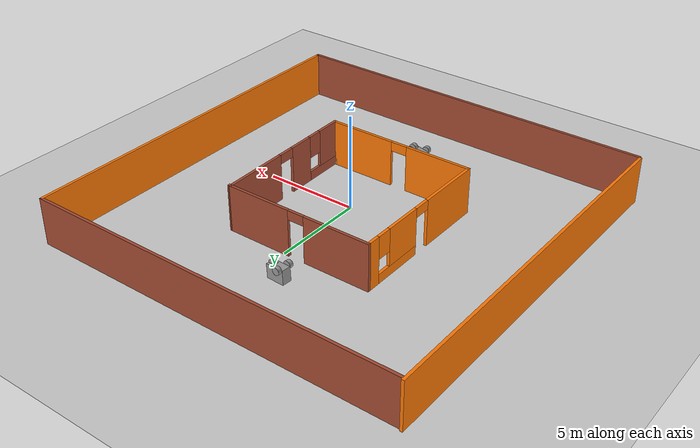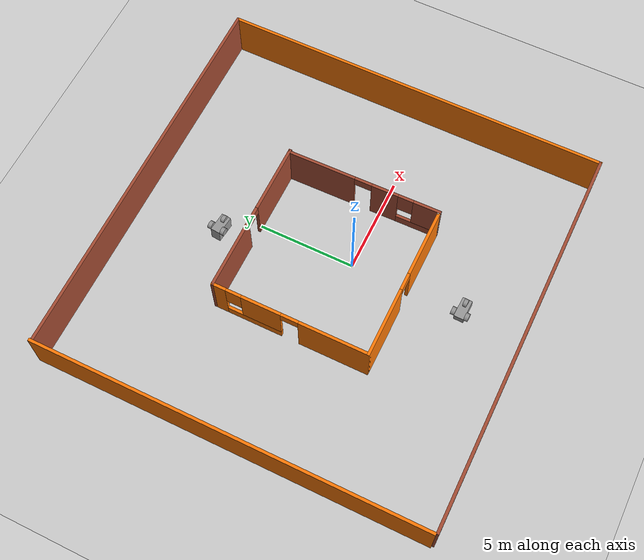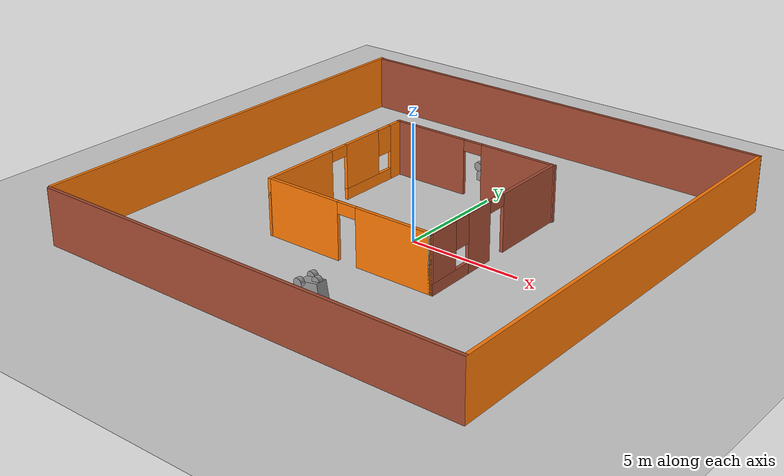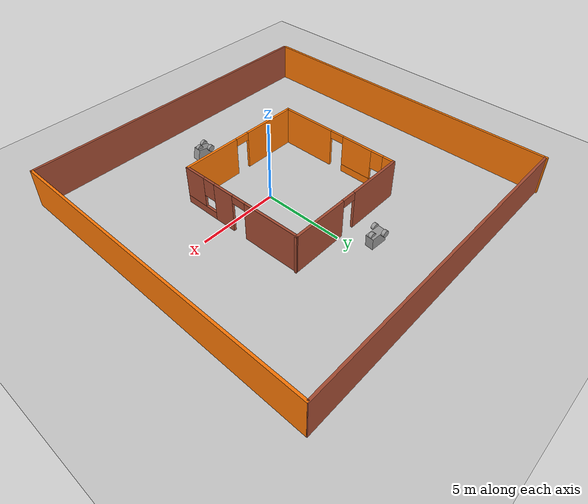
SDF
<sdf version="1.6">
 <world name="default">
  <plugin name="welcome" filename="libwelcome.so"/>
  <model name="ground_plane">
   <static>1</static>
   <link name="link">
    <collision name="collision">
     <geometry><plane><normal>0 0 1</normal><size>100 100</size></plane></geometry>
     <surface><friction><ode><mu>100</mu><mu2>50</mu2></ode></friction></surface>
    </collision>
    <visual name="visual">
     <cast_shadows>0</cast_shadows>
     <geometry><plane><normal>0 0 1</normal><size>100 100</size></plane></geometry>
     <material>
      <script><uri>file://media/materials/scripts/gazebo.material</uri><name>Gazebo/Grey</name></script>
     </material>
    </visual>
   </link>
  </model>
  <gravity>0 0 -9.8</gravity>
  <magnetic_field>6e-06 2.3e-05 -4.2e-05</magnetic_field>
  <atmosphere type="adiabatic"/>
  <physics name="default_physics" default="0" type="ode">
   <max_step_size>0.001</max_step_size>
   <real_time_factor>1</real_time_factor>
   <real_time_update_rate>1000</real_time_update_rate>
  </physics>
  <scene><ambient>0.4 0.4 0.4 1</ambient><background>0.7 0.7 0.7 1</background><shadows>1</shadows></scene>
  <spherical_coordinates>
   <surface_model>EARTH_WGS84</surface_model>
   <latitude_deg>0</latitude_deg>
   <longitude_deg>0</longitude_deg>
   <elevation>0</elevation>
   <heading_deg>0</heading_deg>
  </spherical_coordinates>
  <light name="user_directional_light_0" type="directional">
   <pose>-17.4807 3.50867 1 0 -0 0</pose>
   <diffuse>0.5 0.5 0.5 1</diffuse>
   <specular>0.1 0.1 0.1 1</specular>
   <direction>0.1 0.1 -0.9</direction>
   <attenuation>
    <range>20</range>
    <constant>0.5</constant>
    <linear>0.01</linear>
    <quadratic>0.001</quadratic>
   </attenuation>
  </light>
  <model name="robocar1">
   <link name="front_wheel">
    <pose>-0.3 4 0.2 1.5708 -0 0</pose>
    <inertial>
     <mass>1</mass>
     <inertia><ixx>0.145833</ixx><ixy>0</ixy><ixz>0</ixz><iyy>0.145833</iyy><iyz>0</iyz><izz>0.125</izz></inertia>
     <pose>0 0 0 1.5708 -0 0</pose>
    </inertial>
    <visual name="visual">
     <pose>0 0 0 0 -0 1.5708</pose>
     <geometry><cylinder><radius>0.2</radius><length>0.2</length></cylinder></geometry>
     <material>
      <lighting>1</lighting>
      <script><uri>file://media/materials/scripts/gazebo.material</uri><name>Gazebo/Grey</name></script>
      <shader type="pixel"><normal_map>__default__</normal_map></shader>
      <ambient>0.3 0.3 0.3 1</ambient>
      <diffuse>0.7 0.7 0.7 1</diffuse>
      <specular>0.01 0.01 0.01 1</specular>
      <emissive>0 0 0 1</emissive>
     </material>
    </visual>
    <collision name="collision">
     <geometry><cylinder><radius>0.2</radius><length>0.2</length></cylinder></geometry>
     <surface>
      <friction>
       <ode><mu>1</mu><mu2>1</mu2><fdir1>0 0 0</fdir1><slip1>0</slip1><slip2>0</slip2></ode>
       <torsional>
        <coefficient>1</coefficient>
        <patch_radius>0</patch_radius>
        <surface_radius>0</surface_radius>
        <use_patch_radius>1</use_patch_radius>
        <ode><slip>0</slip></ode>
       </torsional>
      </friction>
      <bounce><restitution_coefficient>0</restitution_coefficient><threshold>1e+06</threshold></bounce>
      <contact>
       <collide_without_contact>0</collide_without_contact>
       <collide_without_contact_bitmask>1</collide_without_contact_bitmask>
       <collide_bitmask>1</collide_bitmask>
       <ode>
        <soft_cfm>0</soft_cfm>
        <soft_erp>0.2</soft_erp>
        <kp>1e+13</kp>
        <kd>1</kd>
        <max_vel>0.01</max_vel>
        <min_depth>0</min_depth>
       </ode>
       <bullet>
        <split_impulse>1</split_impulse>
        <split_impulse_penetration_threshold>-0.01</split_impulse_penetration_threshold>
        <soft_cfm>0</soft_cfm>
        <soft_erp>0.2</soft_erp>
        <kp>1e+13</kp>
        <kd>1</kd>
       </bullet>
      </contact>
     </surface>
    </collision>
   </link>
   <link name="body">
    <pose>0 4 0.575 0 -0 0</pose>
    <inertial>
     <mass>1</mass>
     <inertia>
      <ixx>0.166667</ixx>
      <ixy>0</ixy>
      <ixz>0</ixz>
      <iyy>0.166667</iyy>
      <iyz>0</iyz>
      <izz>0.166667</izz>
     </inertia>
    </inertial>
    <visual name="visual">
     <geometry><box><size>1 0.5 0.75</size></box></geometry>
     <material>
      <lighting>1</lighting>
      <script><uri>file://media/materials/scripts/gazebo.material</uri><name>Gazebo/Grey</name></script>
      <shader type="pixel"><normal_map>__default__</normal_map></shader>
      <ambient>0.3 0.3 0.3 1</ambient>
      <diffuse>0.7 0.7 0.7 1</diffuse>
      <specular>0.01 0.01 0.01 1</specular>
      <emissive>0 0 0 1</emissive>
     </material>
    </visual>
    <collision name="collision">
     <geometry><box><size>1 0.5 0.75</size></box></geometry>
     <surface>
      <friction>
       <ode><mu>1</mu><mu2>1</mu2><fdir1>0 0 0</fdir1><slip1>0</slip1><slip2>0</slip2></ode>
       <torsional>
        <coefficient>1</coefficient>
        <patch_radius>0</patch_radius>
        <surface_radius>0</surface_radius>
        <use_patch_radius>1</use_patch_radius>
        <ode><slip>0</slip></ode>
       </torsional>
      </friction>
      <bounce><restitution_coefficient>0</restitution_coefficient><threshold>1e+06</threshold></bounce>
      <contact>
       <collide_without_contact>0</collide_without_contact>
       <collide_without_contact_bitmask>1</collide_without_contact_bitmask>
       <collide_bitmask>1</collide_bitmask>
       <ode>
        <soft_cfm>0</soft_cfm>
        <soft_erp>0.2</soft_erp>
        <kp>1e+13</kp>
        <kd>1</kd>
        <max_vel>0.01</max_vel>
        <min_depth>0</min_depth>
       </ode>
       <bullet>
        <split_impulse>1</split_impulse>
        <split_impulse_penetration_threshold>-0.01</split_impulse_penetration_threshold>
        <soft_cfm>0</soft_cfm>
        <soft_erp>0.2</soft_erp>
        <kp>1e+13</kp>
        <kd>1</kd>
       </bullet>
      </contact>
     </surface>
    </collision>
   </link>
   <link name="left_wheel">
    <pose>0.3 4.35 0.2 1.5708 -0 0</pose>
    <inertial>
     <mass>1</mass>
     <inertia><ixx>0.145833</ixx><ixy>0</ixy><ixz>0</ixz><iyy>0.145833</iyy><iyz>0</iyz><izz>0.125</izz></inertia>
     <pose>0 0 0 1.5708 -0 0</pose>
    </inertial>
    <visual name="visual">
     <pose>0 0 0 0 -0 1.5708</pose>
     <geometry><cylinder><radius>0.2</radius><length>0.2</length></cylinder></geometry>
     <material>
      <lighting>1</lighting>
      <script><uri>file://media/materials/scripts/gazebo.material</uri><name>Gazebo/Grey</name></script>
      <shader type="pixel"><normal_map>__default__</normal_map></shader>
      <ambient>0.3 0.3 0.3 1</ambient>
      <diffuse>0.7 0.7 0.7 1</diffuse>
      <specular>0.01 0.01 0.01 1</specular>
      <emissive>0 0 0 1</emissive>
     </material>
    </visual>
    <collision name="collision">
     <geometry><cylinder><radius>0.2</radius><length>0.2</length></cylinder></geometry>
     <surface>
      <friction>
       <ode><mu>1</mu><mu2>1</mu2><fdir1>0 0 0</fdir1><slip1>0</slip1><slip2>0</slip2></ode>
       <torsional>
        <coefficient>1</coefficient>
        <patch_radius>0</patch_radius>
        <surface_radius>0</surface_radius>
        <use_patch_radius>1</use_patch_radius>
        <ode><slip>0</slip></ode>
       </torsional>
      </friction>
      <bounce><restitution_coefficient>0</restitution_coefficient><threshold>1e+06</threshold></bounce>
      <contact>
       <collide_without_contact>0</collide_without_contact>
       <collide_without_contact_bitmask>1</collide_without_contact_bitmask>
       <collide_bitmask>1</collide_bitmask>
       <ode>
        <soft_cfm>0</soft_cfm>
        <soft_erp>0.2</soft_erp>
        <kp>1e+13</kp>
        <kd>1</kd>
        <max_vel>0.01</max_vel>
        <min_depth>0</min_depth>
       </ode>
       <bullet>
        <split_impulse>1</split_impulse>
        <split_impulse_penetration_threshold>-0.01</split_impulse_penetration_threshold>
        <soft_cfm>0</soft_cfm>
        <soft_erp>0.2</soft_erp>
        <kp>1e+13</kp>
        <kd>1</kd>
       </bullet>
      </contact>
     </surface>
    </collision>
   </link>
   <link name="right_wheel">
    <pose>0.3 3.65 0.2 1.5708 -0 0</pose>
    <inertial>
     <mass>1</mass>
     <inertia><ixx>0.145833</ixx><ixy>0</ixy><ixz>0</ixz><iyy>0.145833</iyy><iyz>0</iyz><izz>0.125</izz></inertia>
     <pose>0 0 0 1.5708 -0 0</pose>
    </inertial>
    <visual name="visual">
     <pose>0 0 0 0 -0 1.5708</pose>
     <geometry><cylinder><radius>0.2</radius><length>0.2</length></cylinder></geometry>
     <material>
      <lighting>1</lighting>
      <script><uri>file://media/materials/scripts/gazebo.material</uri><name>Gazebo/Grey</name></script>
      <shader type="pixel"><normal_map>__default__</normal_map></shader>
      <ambient>0.3 0.3 0.3 1</ambient>
      <diffuse>0.7 0.7 0.7 1</diffuse>
      <specular>0.01 0.01 0.01 1</specular>
      <emissive>0 0 0 1</emissive>
     </material>
    </visual>
    <collision name="collision">
     <geometry><cylinder><radius>0.2</radius><length>0.2</length></cylinder></geometry>
     <surface>
      <friction>
       <ode><mu>1</mu><mu2>1</mu2><fdir1>0 0 0</fdir1><slip1>0</slip1><slip2>0</slip2></ode>
       <torsional>
        <coefficient>1</coefficient>
        <patch_radius>0</patch_radius>
        <surface_radius>0</surface_radius>
        <use_patch_radius>1</use_patch_radius>
        <ode><slip>0</slip></ode>
       </torsional>
      </friction>
      <bounce><restitution_coefficient>0</restitution_coefficient><threshold>1e+06</threshold></bounce>
      <contact>
       <collide_without_contact>0</collide_without_contact>
       <collide_without_contact_bitmask>1</collide_without_contact_bitmask>
       <collide_bitmask>1</collide_bitmask>
       <ode>
        <soft_cfm>0</soft_cfm>
        <soft_erp>0.2</soft_erp>
        <kp>1e+13</kp>
        <kd>1</kd>
        <max_vel>0.01</max_vel>
        <min_depth>0</min_depth>
       </ode>
       <bullet>
        <split_impulse>1</split_impulse>
        <split_impulse_penetration_threshold>-0.01</split_impulse_penetration_threshold>
        <soft_cfm>0</soft_cfm>
        <soft_erp>0.2</soft_erp>
        <kp>1e+13</kp>
        <kd>1</kd>
       </bullet>
      </contact>
     </surface>
    </collision>
   </link>
   <joint name="front_wheel_joint" type="revolute">
    <parent>body</parent>
    <child>front_wheel</child>
    <axis>
     <xyz>0 0 1</xyz>
     <use_parent_model_frame>0</use_parent_model_frame>
     <limit>
      <lower>-1.79769e+308</lower>
      <upper>1.79769e+308</upper>
      <effort>-1</effort>
      <velocity>-1</velocity>
     </limit>
     <dynamics>
      <spring_reference>0</spring_reference>
      <spring_stiffness>0</spring_stiffness>
      <damping>0</damping>
      <friction>0</friction>
     </dynamics>
    </axis>
    <physics>
     <ode><limit><cfm>0</cfm><erp>0.2</erp></limit><suspension><cfm>0</cfm><erp>0.2</erp></suspension></ode>
    </physics>
   </joint>
   <joint name="left_wheel_joint" type="revolute">
    <parent>body</parent>
    <child>left_wheel</child>
    <axis>
     <xyz>0 0 1</xyz>
     <use_parent_model_frame>0</use_parent_model_frame>
     <limit>
      <lower>-1.79769e+308</lower>
      <upper>1.79769e+308</upper>
      <effort>-1</effort>
      <velocity>-1</velocity>
     </limit>
     <dynamics>
      <spring_reference>0</spring_reference>
      <spring_stiffness>0</spring_stiffness>
      <damping>0</damping>
      <friction>0</friction>
     </dynamics>
    </axis>
    <physics>
     <ode><limit><cfm>0</cfm><erp>0.2</erp></limit><suspension><cfm>0</cfm><erp>0.2</erp></suspension></ode>
    </physics>
   </joint>
   <joint name="right_wheel_joint" type="revolute">
    <parent>body</parent>
    <child>right_wheel</child>
    <axis>
     <xyz>0 0 1</xyz>
     <use_parent_model_frame>0</use_parent_model_frame>
     <limit>
      <lower>-1.79769e+308</lower>
      <upper>1.79769e+308</upper>
      <effort>-1</effort>
      <velocity>-1</velocity>
     </limit>
     <dynamics>
      <spring_reference>0</spring_reference>
      <spring_stiffness>0</spring_stiffness>
      <damping>0</damping>
      <friction>0</friction>
     </dynamics>
    </axis>
    <physics>
     <ode><limit><cfm>0</cfm><erp>0.2</erp></limit><suspension><cfm>0</cfm><erp>0.2</erp></suspension></ode>
    </physics>
   </joint>
   <static>0</static>
   <pose>-1.42424 2.68424 0.965286 3.14159 -0.051894 3.05085</pose>
  </model>
  <model name="robocar2">
   <link name="front_wheel">
    <pose>-0.3 4 0.2 1.5708 -0 0</pose>
    <inertial>
     <mass>1</mass>
     <inertia><ixx>0.145833</ixx><ixy>0</ixy><ixz>0</ixz><iyy>0.145833</iyy><iyz>0</iyz><izz>0.125</izz></inertia>
     <pose>0 0 0 1.5708 -0 0</pose>
    </inertial>
    <visual name="visual">
     <pose>0 0 0 0 -0 1.5708</pose>
     <geometry><cylinder><radius>0.2</radius><length>0.2</length></cylinder></geometry>
     <material>
      <lighting>1</lighting>
      <script><uri>file://media/materials/scripts/gazebo.material</uri><name>Gazebo/Grey</name></script>
      <shader type="pixel"><normal_map>__default__</normal_map></shader>
      <ambient>0.3 0.3 0.3 1</ambient>
      <diffuse>0.7 0.7 0.7 1</diffuse>
      <specular>0.01 0.01 0.01 1</specular>
      <emissive>0 0 0 1</emissive>
     </material>
    </visual>
    <collision name="collision">
     <geometry><cylinder><radius>0.2</radius><length>0.2</length></cylinder></geometry>
     <surface>
      <friction>
       <ode><mu>1</mu><mu2>1</mu2><fdir1>0 0 0</fdir1><slip1>0</slip1><slip2>0</slip2></ode>
       <torsional>
        <coefficient>1</coefficient>
        <patch_radius>0</patch_radius>
        <surface_radius>0</surface_radius>
        <use_patch_radius>1</use_patch_radius>
        <ode><slip>0</slip></ode>
       </torsional>
      </friction>
      <bounce><restitution_coefficient>0</restitution_coefficient><threshold>1e+06</threshold></bounce>
      <contact>
       <collide_without_contact>0</collide_without_contact>
       <collide_without_contact_bitmask>1</collide_without_contact_bitmask>
       <collide_bitmask>1</collide_bitmask>
       <ode>
        <soft_cfm>0</soft_cfm>
        <soft_erp>0.2</soft_erp>
        <kp>1e+13</kp>
        <kd>1</kd>
        <max_vel>0.01</max_vel>
        <min_depth>0</min_depth>
       </ode>
       <bullet>
        <split_impulse>1</split_impulse>
        <split_impulse_penetration_threshold>-0.01</split_impulse_penetration_threshold>
        <soft_cfm>0</soft_cfm>
        <soft_erp>0.2</soft_erp>
        <kp>1e+13</kp>
        <kd>1</kd>
       </bullet>
      </contact>
     </surface>
    </collision>
   </link>
   <link name="body">
    <pose>0 4 0.575 0 -0 0</pose>
    <inertial>
     <mass>1</mass>
     <inertia>
      <ixx>0.166667</ixx>
      <ixy>0</ixy>
      <ixz>0</ixz>
      <iyy>0.166667</iyy>
      <iyz>0</iyz>
      <izz>0.166667</izz>
     </inertia>
    </inertial>
    <visual name="visual">
     <geometry><box><size>1 0.5 0.75</size></box></geometry>
     <material>
      <lighting>1</lighting>
      <script><uri>file://media/materials/scripts/gazebo.material</uri><name>Gazebo/Grey</name></script>
      <shader type="pixel"><normal_map>__default__</normal_map></shader>
      <ambient>0.3 0.3 0.3 1</ambient>
      <diffuse>0.7 0.7 0.7 1</diffuse>
      <specular>0.01 0.01 0.01 1</specular>
      <emissive>0 0 0 1</emissive>
     </material>
    </visual>
    <collision name="collision">
     <geometry><box><size>1 0.5 0.75</size></box></geometry>
     <surface>
      <friction>
       <ode><mu>1</mu><mu2>1</mu2><fdir1>0 0 0</fdir1><slip1>0</slip1><slip2>0</slip2></ode>
       <torsional>
        <coefficient>1</coefficient>
        <patch_radius>0</patch_radius>
        <surface_radius>0</surface_radius>
        <use_patch_radius>1</use_patch_radius>
        <ode><slip>0</slip></ode>
       </torsional>
      </friction>
      <bounce><restitution_coefficient>0</restitution_coefficient><threshold>1e+06</threshold></bounce>
      <contact>
       <collide_without_contact>0</collide_without_contact>
       <collide_without_contact_bitmask>1</collide_without_contact_bitmask>
       <collide_bitmask>1</collide_bitmask>
       <ode>
        <soft_cfm>0</soft_cfm>
        <soft_erp>0.2</soft_erp>
        <kp>1e+13</kp>
        <kd>1</kd>
        <max_vel>0.01</max_vel>
        <min_depth>0</min_depth>
       </ode>
       <bullet>
        <split_impulse>1</split_impulse>
        <split_impulse_penetration_threshold>-0.01</split_impulse_penetration_threshold>
        <soft_cfm>0</soft_cfm>
        <soft_erp>0.2</soft_erp>
        <kp>1e+13</kp>
        <kd>1</kd>
       </bullet>
      </contact>
     </surface>
    </collision>
   </link>
   <link name="left_wheel">
    <pose>0.3 4.35 0.2 1.5708 -0 0</pose>
    <inertial>
     <mass>1</mass>
     <inertia><ixx>0.145833</ixx><ixy>0</ixy><ixz>0</ixz><iyy>0.145833</iyy><iyz>0</iyz><izz>0.125</izz></inertia>
     <pose>0 0 0 1.5708 -0 0</pose>
    </inertial>
    <visual name="visual">
     <pose>0 0 0 0 -0 1.5708</pose>
     <geometry><cylinder><radius>0.2</radius><length>0.2</length></cylinder></geometry>
     <material>
      <lighting>1</lighting>
      <script><uri>file://media/materials/scripts/gazebo.material</uri><name>Gazebo/Grey</name></script>
      <shader type="pixel"><normal_map>__default__</normal_map></shader>
      <ambient>0.3 0.3 0.3 1</ambient>
      <diffuse>0.7 0.7 0.7 1</diffuse>
      <specular>0.01 0.01 0.01 1</specular>
      <emissive>0 0 0 1</emissive>
     </material>
    </visual>
    <collision name="collision">
     <geometry><cylinder><radius>0.2</radius><length>0.2</length></cylinder></geometry>
     <surface>
      <friction>
       <ode><mu>1</mu><mu2>1</mu2><fdir1>0 0 0</fdir1><slip1>0</slip1><slip2>0</slip2></ode>
       <torsional>
        <coefficient>1</coefficient>
        <patch_radius>0</patch_radius>
        <surface_radius>0</surface_radius>
        <use_patch_radius>1</use_patch_radius>
        <ode><slip>0</slip></ode>
       </torsional>
      </friction>
      <bounce><restitution_coefficient>0</restitution_coefficient><threshold>1e+06</threshold></bounce>
      <contact>
       <collide_without_contact>0</collide_without_contact>
       <collide_without_contact_bitmask>1</collide_without_contact_bitmask>
       <collide_bitmask>1</collide_bitmask>
       <ode>
        <soft_cfm>0</soft_cfm>
        <soft_erp>0.2</soft_erp>
        <kp>1e+13</kp>
        <kd>1</kd>
        <max_vel>0.01</max_vel>
        <min_depth>0</min_depth>
       </ode>
       <bullet>
        <split_impulse>1</split_impulse>
        <split_impulse_penetration_threshold>-0.01</split_impulse_penetration_threshold>
        <soft_cfm>0</soft_cfm>
        <soft_erp>0.2</soft_erp>
        <kp>1e+13</kp>
        <kd>1</kd>
       </bullet>
      </contact>
     </surface>
    </collision>
   </link>
   <link name="right_wheel">
    <pose>0.3 3.65 0.2 1.5708 -0 0</pose>
    <inertial>
     <mass>1</mass>
     <inertia><ixx>0.145833</ixx><ixy>0</ixy><ixz>0</ixz><iyy>0.145833</iyy><iyz>0</iyz><izz>0.125</izz></inertia>
     <pose>0 0 0 1.5708 -0 0</pose>
    </inertial>
    <visual name="visual">
     <pose>0 0 0 0 -0 1.5708</pose>
     <geometry><cylinder><radius>0.2</radius><length>0.2</length></cylinder></geometry>
     <material>
      <lighting>1</lighting>
      <script><uri>file://media/materials/scripts/gazebo.material</uri><name>Gazebo/Grey</name></script>
      <shader type="pixel"><normal_map>__default__</normal_map></shader>
      <ambient>0.3 0.3 0.3 1</ambient>
      <diffuse>0.7 0.7 0.7 1</diffuse>
      <specular>0.01 0.01 0.01 1</specular>
      <emissive>0 0 0 1</emissive>
     </material>
    </visual>
    <collision name="collision">
     <geometry><cylinder><radius>0.2</radius><length>0.2</length></cylinder></geometry>
     <surface>
      <friction>
       <ode><mu>1</mu><mu2>1</mu2><fdir1>0 0 0</fdir1><slip1>0</slip1><slip2>0</slip2></ode>
       <torsional>
        <coefficient>1</coefficient>
        <patch_radius>0</patch_radius>
        <surface_radius>0</surface_radius>
        <use_patch_radius>1</use_patch_radius>
        <ode><slip>0</slip></ode>
       </torsional>
      </friction>
      <bounce><restitution_coefficient>0</restitution_coefficient><threshold>1e+06</threshold></bounce>
      <contact>
       <collide_without_contact>0</collide_without_contact>
       <collide_without_contact_bitmask>1</collide_without_contact_bitmask>
       <collide_bitmask>1</collide_bitmask>
       <ode>
        <soft_cfm>0</soft_cfm>
        <soft_erp>0.2</soft_erp>
        <kp>1e+13</kp>
        <kd>1</kd>
        <max_vel>0.01</max_vel>
        <min_depth>0</min_depth>
       </ode>
       <bullet>
        <split_impulse>1</split_impulse>
        <split_impulse_penetration_threshold>-0.01</split_impulse_penetration_threshold>
        <soft_cfm>0</soft_cfm>
        <soft_erp>0.2</soft_erp>
        <kp>1e+13</kp>
        <kd>1</kd>
       </bullet>
      </contact>
     </surface>
    </collision>
   </link>
   <joint name="front_wheel_joint" type="revolute">
    <parent>body</parent>
    <child>front_wheel</child>
    <axis>
     <xyz>0 0 1</xyz>
     <use_parent_model_frame>0</use_parent_model_frame>
     <limit>
      <lower>-1.79769e+308</lower>
      <upper>1.79769e+308</upper>
      <effort>-1</effort>
      <velocity>-1</velocity>
     </limit>
     <dynamics>
      <spring_reference>0</spring_reference>
      <spring_stiffness>0</spring_stiffness>
      <damping>0</damping>
      <friction>0</friction>
     </dynamics>
    </axis>
    <physics>
     <ode><limit><cfm>0</cfm><erp>0.2</erp></limit><suspension><cfm>0</cfm><erp>0.2</erp></suspension></ode>
    </physics>
   </joint>
   <joint name="left_wheel_joint" type="revolute">
    <parent>body</parent>
    <child>left_wheel</child>
    <axis>
     <xyz>0 0 1</xyz>
     <use_parent_model_frame>0</use_parent_model_frame>
     <limit>
      <lower>-1.79769e+308</lower>
      <upper>1.79769e+308</upper>
      <effort>-1</effort>
      <velocity>-1</velocity>
     </limit>
     <dynamics>
      <spring_reference>0</spring_reference>
      <spring_stiffness>0</spring_stiffness>
      <damping>0</damping>
      <friction>0</friction>
     </dynamics>
    </axis>
    <physics>
     <ode><limit><cfm>0</cfm><erp>0.2</erp></limit><suspension><cfm>0</cfm><erp>0.2</erp></suspension></ode>
    </physics>
   </joint>
   <joint name="right_wheel_joint" type="revolute">
    <parent>body</parent>
    <child>right_wheel</child>
    <axis>
     <xyz>0 0 1</xyz>
     <use_parent_model_frame>0</use_parent_model_frame>
     <limit>
      <lower>-1.79769e+308</lower>
      <upper>1.79769e+308</upper>
      <effort>-1</effort>
      <velocity>-1</velocity>
     </limit>
     <dynamics>
      <spring_reference>0</spring_reference>
      <spring_stiffness>0</spring_stiffness>
      <damping>0</damping>
      <friction>0</friction>
     </dynamics>
    </axis>
    <physics>
     <ode><limit><cfm>0</cfm><erp>0.2</erp></limit><suspension><cfm>0</cfm><erp>0.2</erp></suspension></ode>
    </physics>
   </joint>
   <static>0</static>
   <pose>-0.228085 -9.85361 0.890215 -3.14159 0.188592 3.10052</pose>
  </model>
  <model name="walls">
   <link name="Wall_44">
    <pose>0 -10 0 0 -0 0</pose>
    <inertial>
     <mass>1</mass>
     <inertia><ixx>1</ixx><ixy>0</ixy><ixz>0</ixz><iyy>1</iyy><iyz>0</iyz><izz>1</izz></inertia>
    </inertial>
    <visual name="Wall_44_Visual">
     <pose>0 0 1.25 0 -0 0</pose>
     <geometry><box><size>20.15 0.15 2.5</size></box></geometry>
     <material>
      <script><uri>file://media/materials/scripts/gazebo.material</uri><name>Gazebo/Bricks</name></script>
      <ambient>0.761 0.663 0.627 1</ambient>
      <shader type="pixel"><normal_map>__default__</normal_map></shader>
      <diffuse>1 1 1 1</diffuse>
      <specular>0.2 0.2 0.2 1</specular>
      <emissive>0 0 0 1</emissive>
     </material>
     <meta><layer>0</layer></meta>
    </visual>
    <collision name="Wall_44_Collision">
     <pose>0 0 1.25 0 -0 0</pose>
     <geometry><box><size>20.15 0.15 2.5</size></box></geometry>
     <surface>
      <friction>
       <ode><mu>1</mu><mu2>1</mu2><fdir1>0 0 0</fdir1><slip1>0</slip1><slip2>0</slip2></ode>
       <torsional>
        <coefficient>1</coefficient>
        <patch_radius>0</patch_radius>
        <surface_radius>0</surface_radius>
        <use_patch_radius>1</use_patch_radius>
        <ode><slip>0</slip></ode>
       </torsional>
      </friction>
      <bounce><restitution_coefficient>0</restitution_coefficient><threshold>1e+06</threshold></bounce>
      <contact>
       <collide_without_contact>0</collide_without_contact>
       <collide_without_contact_bitmask>1</collide_without_contact_bitmask>
       <collide_bitmask>1</collide_bitmask>
       <ode>
        <soft_cfm>0</soft_cfm>
        <soft_erp>0.2</soft_erp>
        <kp>1e+13</kp>
        <kd>1</kd>
        <max_vel>0.01</max_vel>
        <min_depth>0</min_depth>
       </ode>
       <bullet>
        <split_impulse>1</split_impulse>
        <split_impulse_penetration_threshold>-0.01</split_impulse_penetration_threshold>
        <soft_cfm>0</soft_cfm>
        <soft_erp>0.2</soft_erp>
        <kp>1e+13</kp>
        <kd>1</kd>
       </bullet>
      </contact>
     </surface>
    </collision>
   </link>
   <link name="Wall_44_clone">
    <pose>-0.011522 10.0457 0 0 -0 0</pose>
    <inertial>
     <mass>1</mass>
     <inertia><ixx>1</ixx><ixy>0</ixy><ixz>0</ixz><iyy>1</iyy><iyz>0</iyz><izz>1</izz></inertia>
    </inertial>
    <visual name="Wall_44_Visual">
     <pose>0 0 1.25 0 -0 0</pose>
     <geometry><box><size>20.15 0.15 2.5</size></box></geometry>
     <material>
      <script><uri>file://media/materials/scripts/gazebo.material</uri><name>Gazebo/Bricks</name></script>
      <ambient>0.761 0.663 0.627 1</ambient>
      <shader type="pixel"><normal_map>__default__</normal_map></shader>
      <diffuse>1 1 1 1</diffuse>
      <specular>0.2 0.2 0.2 1</specular>
      <emissive>0 0 0 1</emissive>
     </material>
     <meta><layer>0</layer></meta>
    </visual>
    <collision name="Wall_44_Collision">
     <pose>0 0 1.25 0 -0 0</pose>
     <geometry><box><size>20.15 0.15 2.5</size></box></geometry>
     <surface>
      <friction>
       <ode><mu>1</mu><mu2>1</mu2><fdir1>0 0 0</fdir1><slip1>0</slip1><slip2>0</slip2></ode>
       <torsional>
        <coefficient>1</coefficient>
        <patch_radius>0</patch_radius>
        <surface_radius>0</surface_radius>
        <use_patch_radius>1</use_patch_radius>
        <ode><slip>0</slip></ode>
       </torsional>
      </friction>
      <bounce><restitution_coefficient>0</restitution_coefficient><threshold>1e+06</threshold></bounce>
      <contact>
       <collide_without_contact>0</collide_without_contact>
       <collide_without_contact_bitmask>1</collide_without_contact_bitmask>
       <collide_bitmask>1</collide_bitmask>
       <ode>
        <soft_cfm>0</soft_cfm>
        <soft_erp>0.2</soft_erp>
        <kp>1e+13</kp>
        <kd>1</kd>
        <max_vel>0.01</max_vel>
        <min_depth>0</min_depth>
       </ode>
       <bullet>
        <split_impulse>1</split_impulse>
        <split_impulse_penetration_threshold>-0.01</split_impulse_penetration_threshold>
        <soft_cfm>0</soft_cfm>
        <soft_erp>0.2</soft_erp>
        <kp>1e+13</kp>
        <kd>1</kd>
       </bullet>
      </contact>
     </surface>
    </collision>
   </link>
   <link name="Wall_45">
    <pose>10 0 0 0 -0 1.5708</pose>
    <visual name="Wall_45_Visual">
     <pose>0 0 1.25 0 -0 0</pose>
     <geometry><box><size>20.15 0.15 2.5</size></box></geometry>
     <material>
      <script><uri>file://media/materials/scripts/gazebo.material</uri><name>Gazebo/Grey</name></script>
      <ambient>0.996078 0.47451 0.0196078 1</ambient>
      <shader type="pixel"/>
      <diffuse>0.7 0.7 0.7 1</diffuse>
      <specular>0.01 0.01 0.01 1</specular>
      <emissive>0 0 0 1</emissive>
     </material>
     <meta><layer>0</layer></meta>
    </visual>
    <collision name="Wall_45_Collision">
     <pose>0 0 1.25 0 -0 0</pose>
     <geometry><box><size>20.15 0.15 2.5</size></box></geometry>
     <surface>
      <friction>
       <ode><mu>1</mu><mu2>1</mu2><fdir1>0 0 0</fdir1><slip1>0</slip1><slip2>0</slip2></ode>
       <torsional>
        <coefficient>1</coefficient>
        <patch_radius>0</patch_radius>
        <surface_radius>0</surface_radius>
        <use_patch_radius>1</use_patch_radius>
        <ode><slip>0</slip></ode>
       </torsional>
      </friction>
      <bounce><restitution_coefficient>0</restitution_coefficient><threshold>1e+06</threshold></bounce>
      <contact>
       <collide_without_contact>0</collide_without_contact>
       <collide_without_contact_bitmask>1</collide_without_contact_bitmask>
       <collide_bitmask>1</collide_bitmask>
       <ode>
        <soft_cfm>0</soft_cfm>
        <soft_erp>0.2</soft_erp>
        <kp>1e+13</kp>
        <kd>1</kd>
        <max_vel>0.01</max_vel>
        <min_depth>0</min_depth>
       </ode>
       <bullet>
        <split_impulse>1</split_impulse>
        <split_impulse_penetration_threshold>-0.01</split_impulse_penetration_threshold>
        <soft_cfm>0</soft_cfm>
        <soft_erp>0.2</soft_erp>
        <kp>1e+13</kp>
        <kd>1</kd>
       </bullet>
      </contact>
     </surface>
    </collision>
   </link>
   <link name="Wall_45_clone">
    <pose>-10.0927 0.116806 0 0 -0 1.5708</pose>
    <visual name="Wall_45_Visual">
     <pose>0 0 1.25 0 -0 0</pose>
     <geometry><box><size>20.15 0.15 2.5</size></box></geometry>
     <material>
      <script><uri>file://media/materials/scripts/gazebo.material</uri><name>Gazebo/Grey</name></script>
      <ambient>0.996078 0.47451 0.0196078 1</ambient>
      <shader type="pixel"/>
      <diffuse>0.7 0.7 0.7 1</diffuse>
      <specular>0.01 0.01 0.01 1</specular>
      <emissive>0 0 0 1</emissive>
     </material>
     <meta><layer>0</layer></meta>
    </visual>
    <collision name="Wall_45_Collision">
     <pose>0 0 1.25 0 -0 0</pose>
     <geometry><box><size>20.15 0.15 2.5</size></box></geometry>
     <surface>
      <friction>
       <ode><mu>1</mu><mu2>1</mu2><fdir1>0 0 0</fdir1><slip1>0</slip1><slip2>0</slip2></ode>
       <torsional>
        <coefficient>1</coefficient>
        <patch_radius>0</patch_radius>
        <surface_radius>0</surface_radius>
        <use_patch_radius>1</use_patch_radius>
        <ode><slip>0</slip></ode>
       </torsional>
      </friction>
      <bounce><restitution_coefficient>0</restitution_coefficient><threshold>1e+06</threshold></bounce>
      <contact>
       <collide_without_contact>0</collide_without_contact>
       <collide_without_contact_bitmask>1</collide_without_contact_bitmask>
       <collide_bitmask>1</collide_bitmask>
       <ode>
        <soft_cfm>0</soft_cfm>
        <soft_erp>0.2</soft_erp>
        <kp>1e+13</kp>
        <kd>1</kd>
        <max_vel>0.01</max_vel>
        <min_depth>0</min_depth>
       </ode>
       <bullet>
        <split_impulse>1</split_impulse>
        <split_impulse_penetration_threshold>-0.01</split_impulse_penetration_threshold>
        <soft_cfm>0</soft_cfm>
        <soft_erp>0.2</soft_erp>
        <kp>1e+13</kp>
        <kd>1</kd>
       </bullet>
      </contact>
     </surface>
    </collision>
   </link>
   <link name="Wall_49">
    <pose>-4 0 0 0 0 -1.5708</pose>
    <visual name="Wall_49_Visual_0">
     <pose>-3.69081 0 1.25 0 -0 0</pose>
     <geometry><box><size>0.768371 0.15 2.5</size></box></geometry>
     <material>
      <script><uri>file://media/materials/scripts/gazebo.material</uri><name>Gazebo/Grey</name></script>
      <ambient>0.996078 0.47451 0.0196078 1</ambient>
      <shader type="pixel"/>
      <diffuse>0.7 0.7 0.7 1</diffuse>
      <specular>0.01 0.01 0.01 1</specular>
      <emissive>0 0 0 1</emissive>
     </material>
     <meta><layer>0</layer></meta>
    </visual>
    <visual name="Wall_49_Visual_5">
     <pose>0 0 2.25 0 -0 0</pose>
     <geometry><box><size>0.9 0.15 0.5</size></box></geometry>
     <material>
      <script><uri>file://media/materials/scripts/gazebo.material</uri><name>Gazebo/Grey</name></script>
      <ambient>0.996078 0.47451 0.0196078 1</ambient>
      <shader type="pixel"/>
      <diffuse>0.7 0.7 0.7 1</diffuse>
      <specular>0.01 0.01 0.01 1</specular>
      <emissive>0 0 0 1</emissive>
     </material>
     <meta><layer>0</layer></meta>
    </visual>
    <visual name="Wall_49_Visual_4">
     <pose>-2.90663 0 1.9 0 -0 0</pose>
     <geometry><box><size>0.8 0.15 1.2</size></box></geometry>
     <material>
      <script><uri>file://media/materials/scripts/gazebo.material</uri><name>Gazebo/Grey</name></script>
      <ambient>0.996078 0.47451 0.0196078 1</ambient>
      <shader type="pixel"/>
      <diffuse>0.7 0.7 0.7 1</diffuse>
      <specular>0.01 0.01 0.01 1</specular>
      <emissive>0 0 0 1</emissive>
     </material>
     <meta><layer>0</layer></meta>
    </visual>
    <visual name="Wall_49_Visual_3">
     <pose>-1.47831 0 1.5 0 -0 0</pose>
     <geometry><box><size>2.05663 0.15 2</size></box></geometry>
     <material>
      <script><uri>file://media/materials/scripts/gazebo.material</uri><name>Gazebo/Grey</name></script>
      <ambient>0.996078 0.47451 0.0196078 1</ambient>
      <shader type="pixel"/>
      <diffuse>0.7 0.7 0.7 1</diffuse>
      <specular>0.01 0.01 0.01 1</specular>
      <emissive>0 0 0 1</emissive>
     </material>
     <meta><layer>0</layer></meta>
    </visual>
    <visual name="Wall_49_Visual_1">
     <pose>2.2625 0 1.25 0 -0 0</pose>
     <geometry><box><size>3.625 0.15 2.5</size></box></geometry>
     <material>
      <script><uri>file://media/materials/scripts/gazebo.material</uri><name>Gazebo/Grey</name></script>
      <ambient>0.996078 0.47451 0.0196078 1</ambient>
      <shader type="pixel"/>
      <diffuse>0.7 0.7 0.7 1</diffuse>
      <specular>0.01 0.01 0.01 1</specular>
      <emissive>0 0 0 1</emissive>
     </material>
     <meta><layer>0</layer></meta>
    </visual>
    <visual name="Wall_49_Visual_2">
     <pose>-1.87831 0 0.25 0 -0 0</pose>
     <geometry><box><size>2.85663 0.15 0.5</size></box></geometry>
     <material>
      <script><uri>file://media/materials/scripts/gazebo.material</uri><name>Gazebo/Grey</name></script>
      <ambient>0.996078 0.47451 0.0196078 1</ambient>
      <shader type="pixel"/>
      <diffuse>0.7 0.7 0.7 1</diffuse>
      <specular>0.01 0.01 0.01 1</specular>
      <emissive>0 0 0 1</emissive>
     </material>
     <meta><layer>0</layer></meta>
    </visual>
    <collision name="Wall_49_Collision_2">
     <pose>-1.87831 0 0.25 0 -0 0</pose>
     <geometry><box><size>2.85663 0.15 0.5</size></box></geometry>
     <surface>
      <friction>
       <ode><mu>1</mu><mu2>1</mu2><fdir1>0 0 0</fdir1><slip1>0</slip1><slip2>0</slip2></ode>
       <torsional>
        <coefficient>1</coefficient>
        <patch_radius>0</patch_radius>
        <surface_radius>0</surface_radius>
        <use_patch_radius>1</use_patch_radius>
        <ode><slip>0</slip></ode>
       </torsional>
      </friction>
      <bounce><restitution_coefficient>0</restitution_coefficient><threshold>1e+06</threshold></bounce>
      <contact>
       <collide_without_contact>0</collide_without_contact>
       <collide_without_contact_bitmask>1</collide_without_contact_bitmask>
       <collide_bitmask>1</collide_bitmask>
       <ode>
        <soft_cfm>0</soft_cfm>
        <soft_erp>0.2</soft_erp>
        <kp>1e+13</kp>
        <kd>1</kd>
        <max_vel>0.01</max_vel>
        <min_depth>0</min_depth>
       </ode>
       <bullet>
        <split_impulse>1</split_impulse>
        <split_impulse_penetration_threshold>-0.01</split_impulse_penetration_threshold>
        <soft_cfm>0</soft_cfm>
        <soft_erp>0.2</soft_erp>
        <kp>1e+13</kp>
        <kd>1</kd>
       </bullet>
      </contact>
     </surface>
    </collision>
    <collision name="Wall_49_Collision_4">
     <pose>-2.90663 0 1.9 0 -0 0</pose>
     <geometry><box><size>0.8 0.15 1.2</size></box></geometry>
     <surface>
      <friction>
       <ode><mu>1</mu><mu2>1</mu2><fdir1>0 0 0</fdir1><slip1>0</slip1><slip2>0</slip2></ode>
       <torsional>
        <coefficient>1</coefficient>
        <patch_radius>0</patch_radius>
        <surface_radius>0</surface_radius>
        <use_patch_radius>1</use_patch_radius>
        <ode><slip>0</slip></ode>
       </torsional>
      </friction>
      <bounce><restitution_coefficient>0</restitution_coefficient><threshold>1e+06</threshold></bounce>
      <contact>
       <collide_without_contact>0</collide_without_contact>
       <collide_without_contact_bitmask>1</collide_without_contact_bitmask>
       <collide_bitmask>1</collide_bitmask>
       <ode>
        <soft_cfm>0</soft_cfm>
        <soft_erp>0.2</soft_erp>
        <kp>1e+13</kp>
        <kd>1</kd>
        <max_vel>0.01</max_vel>
        <min_depth>0</min_depth>
       </ode>
       <bullet>
        <split_impulse>1</split_impulse>
        <split_impulse_penetration_threshold>-0.01</split_impulse_penetration_threshold>
        <soft_cfm>0</soft_cfm>
        <soft_erp>0.2</soft_erp>
        <kp>1e+13</kp>
        <kd>1</kd>
       </bullet>
      </contact>
     </surface>
    </collision>
    <collision name="Wall_49_Collision_1">
     <pose>2.2625 0 1.25 0 -0 0</pose>
     <geometry><box><size>3.625 0.15 2.5</size></box></geometry>
     <surface>
      <friction>
       <ode><mu>1</mu><mu2>1</mu2><fdir1>0 0 0</fdir1><slip1>0</slip1><slip2>0</slip2></ode>
       <torsional>
        <coefficient>1</coefficient>
        <patch_radius>0</patch_radius>
        <surface_radius>0</surface_radius>
        <use_patch_radius>1</use_patch_radius>
        <ode><slip>0</slip></ode>
       </torsional>
      </friction>
      <bounce><restitution_coefficient>0</restitution_coefficient><threshold>1e+06</threshold></bounce>
      <contact>
       <collide_without_contact>0</collide_without_contact>
       <collide_without_contact_bitmask>1</collide_without_contact_bitmask>
       <collide_bitmask>1</collide_bitmask>
       <ode>
        <soft_cfm>0</soft_cfm>
        <soft_erp>0.2</soft_erp>
        <kp>1e+13</kp>
        <kd>1</kd>
        <max_vel>0.01</max_vel>
        <min_depth>0</min_depth>
       </ode>
       <bullet>
        <split_impulse>1</split_impulse>
        <split_impulse_penetration_threshold>-0.01</split_impulse_penetration_threshold>
        <soft_cfm>0</soft_cfm>
        <soft_erp>0.2</soft_erp>
        <kp>1e+13</kp>
        <kd>1</kd>
       </bullet>
      </contact>
     </surface>
    </collision>
    <collision name="Wall_49_Collision_5">
     <pose>0 0 2.25 0 -0 0</pose>
     <geometry><box><size>0.9 0.15 0.5</size></box></geometry>
     <surface>
      <friction>
       <ode><mu>1</mu><mu2>1</mu2><fdir1>0 0 0</fdir1><slip1>0</slip1><slip2>0</slip2></ode>
       <torsional>
        <coefficient>1</coefficient>
        <patch_radius>0</patch_radius>
        <surface_radius>0</surface_radius>
        <use_patch_radius>1</use_patch_radius>
        <ode><slip>0</slip></ode>
       </torsional>
      </friction>
      <bounce><restitution_coefficient>0</restitution_coefficient><threshold>1e+06</threshold></bounce>
      <contact>
       <collide_without_contact>0</collide_without_contact>
       <collide_without_contact_bitmask>1</collide_without_contact_bitmask>
       <collide_bitmask>1</collide_bitmask>
       <ode>
        <soft_cfm>0</soft_cfm>
        <soft_erp>0.2</soft_erp>
        <kp>1e+13</kp>
        <kd>1</kd>
        <max_vel>0.01</max_vel>
        <min_depth>0</min_depth>
       </ode>
       <bullet>
        <split_impulse>1</split_impulse>
        <split_impulse_penetration_threshold>-0.01</split_impulse_penetration_threshold>
        <soft_cfm>0</soft_cfm>
        <soft_erp>0.2</soft_erp>
        <kp>1e+13</kp>
        <kd>1</kd>
       </bullet>
      </contact>
     </surface>
    </collision>
    <collision name="Wall_49_Collision_3">
     <pose>-1.47831 0 1.5 0 -0 0</pose>
     <geometry><box><size>2.05663 0.15 2</size></box></geometry>
     <surface>
      <friction>
       <ode><mu>1</mu><mu2>1</mu2><fdir1>0 0 0</fdir1><slip1>0</slip1><slip2>0</slip2></ode>
       <torsional>
        <coefficient>1</coefficient>
        <patch_radius>0</patch_radius>
        <surface_radius>0</surface_radius>
        <use_patch_radius>1</use_patch_radius>
        <ode><slip>0</slip></ode>
       </torsional>
      </friction>
      <bounce><restitution_coefficient>0</restitution_coefficient><threshold>1e+06</threshold></bounce>
      <contact>
       <collide_without_contact>0</collide_without_contact>
       <collide_without_contact_bitmask>1</collide_without_contact_bitmask>
       <collide_bitmask>1</collide_bitmask>
       <ode>
        <soft_cfm>0</soft_cfm>
        <soft_erp>0.2</soft_erp>
        <kp>1e+13</kp>
        <kd>1</kd>
        <max_vel>0.01</max_vel>
        <min_depth>0</min_depth>
       </ode>
       <bullet>
        <split_impulse>1</split_impulse>
        <split_impulse_penetration_threshold>-0.01</split_impulse_penetration_threshold>
        <soft_cfm>0</soft_cfm>
        <soft_erp>0.2</soft_erp>
        <kp>1e+13</kp>
        <kd>1</kd>
       </bullet>
      </contact>
     </surface>
    </collision>
    <collision name="Wall_49_Collision_0">
     <pose>-3.69081 0 1.25 0 -0 0</pose>
     <geometry><box><size>0.768371 0.15 2.5</size></box></geometry>
     <surface>
      <friction>
       <ode><mu>1</mu><mu2>1</mu2><fdir1>0 0 0</fdir1><slip1>0</slip1><slip2>0</slip2></ode>
       <torsional>
        <coefficient>1</coefficient>
        <patch_radius>0</patch_radius>
        <surface_radius>0</surface_radius>
        <use_patch_radius>1</use_patch_radius>
        <ode><slip>0</slip></ode>
       </torsional>
      </friction>
      <bounce><restitution_coefficient>0</restitution_coefficient><threshold>1e+06</threshold></bounce>
      <contact>
       <collide_without_contact>0</collide_without_contact>
       <collide_without_contact_bitmask>1</collide_without_contact_bitmask>
       <collide_bitmask>1</collide_bitmask>
       <ode>
        <soft_cfm>0</soft_cfm>
        <soft_erp>0.2</soft_erp>
        <kp>1e+13</kp>
        <kd>1</kd>
        <max_vel>0.01</max_vel>
        <min_depth>0</min_depth>
       </ode>
       <bullet>
        <split_impulse>1</split_impulse>
        <split_impulse_penetration_threshold>-0.01</split_impulse_penetration_threshold>
        <soft_cfm>0</soft_cfm>
        <soft_erp>0.2</soft_erp>
        <kp>1e+13</kp>
        <kd>1</kd>
       </bullet>
      </contact>
     </surface>
    </collision>
   </link>
   <link name="Wall_50">
    <pose>0 -4 0 0 -0 0</pose>
    <visual name="Wall_50_Visual_2">
     <pose>0 0 2.25 0 -0 0</pose>
     <geometry><box><size>0.9 0.15 0.5</size></box></geometry>
     <material>
      <script><uri>file://media/materials/scripts/gazebo.material</uri><name>Gazebo/Grey</name></script>
      <ambient>0.996078 0.47451 0.0196078 1</ambient>
      <shader type="pixel"/>
      <diffuse>0.7 0.7 0.7 1</diffuse>
      <specular>0.01 0.01 0.01 1</specular>
      <emissive>0 0 0 1</emissive>
     </material>
     <meta><layer>0</layer></meta>
    </visual>
    <visual name="Wall_50_Visual_0">
     <pose>-2.2625 0 1.25 0 -0 0</pose>
     <geometry><box><size>3.625 0.15 2.5</size></box></geometry>
     <material>
      <script><uri>file://media/materials/scripts/gazebo.material</uri><name>Gazebo/Grey</name></script>
      <ambient>0.996078 0.47451 0.0196078 1</ambient>
      <shader type="pixel"/>
      <diffuse>0.7 0.7 0.7 1</diffuse>
      <specular>0.01 0.01 0.01 1</specular>
      <emissive>0 0 0 1</emissive>
     </material>
     <meta><layer>0</layer></meta>
    </visual>
    <visual name="Wall_50_Visual_1">
     <pose>2.2625 0 1.25 0 -0 0</pose>
     <geometry><box><size>3.625 0.15 2.5</size></box></geometry>
     <material>
      <script><uri>file://media/materials/scripts/gazebo.material</uri><name>Gazebo/Grey</name></script>
      <ambient>0.996078 0.47451 0.0196078 1</ambient>
      <shader type="pixel"/>
      <diffuse>0.7 0.7 0.7 1</diffuse>
      <specular>0.01 0.01 0.01 1</specular>
      <emissive>0 0 0 1</emissive>
     </material>
     <meta><layer>0</layer></meta>
    </visual>
    <collision name="Wall_50_Collision_1">
     <pose>2.2625 0 1.25 0 -0 0</pose>
     <geometry><box><size>3.625 0.15 2.5</size></box></geometry>
     <surface>
      <friction>
       <ode><mu>1</mu><mu2>1</mu2><fdir1>0 0 0</fdir1><slip1>0</slip1><slip2>0</slip2></ode>
       <torsional>
        <coefficient>1</coefficient>
        <patch_radius>0</patch_radius>
        <surface_radius>0</surface_radius>
        <use_patch_radius>1</use_patch_radius>
        <ode><slip>0</slip></ode>
       </torsional>
      </friction>
      <bounce><restitution_coefficient>0</restitution_coefficient><threshold>1e+06</threshold></bounce>
      <contact>
       <collide_without_contact>0</collide_without_contact>
       <collide_without_contact_bitmask>1</collide_without_contact_bitmask>
       <collide_bitmask>1</collide_bitmask>
       <ode>
        <soft_cfm>0</soft_cfm>
        <soft_erp>0.2</soft_erp>
        <kp>1e+13</kp>
        <kd>1</kd>
        <max_vel>0.01</max_vel>
        <min_depth>0</min_depth>
       </ode>
       <bullet>
        <split_impulse>1</split_impulse>
        <split_impulse_penetration_threshold>-0.01</split_impulse_penetration_threshold>
        <soft_cfm>0</soft_cfm>
        <soft_erp>0.2</soft_erp>
        <kp>1e+13</kp>
        <kd>1</kd>
       </bullet>
      </contact>
     </surface>
    </collision>
    <collision name="Wall_50_Collision_0">
     <pose>-2.2625 0 1.25 0 -0 0</pose>
     <geometry><box><size>3.625 0.15 2.5</size></box></geometry>
     <surface>
      <friction>
       <ode><mu>1</mu><mu2>1</mu2><fdir1>0 0 0</fdir1><slip1>0</slip1><slip2>0</slip2></ode>
       <torsional>
        <coefficient>1</coefficient>
        <patch_radius>0</patch_radius>
        <surface_radius>0</surface_radius>
        <use_patch_radius>1</use_patch_radius>
        <ode><slip>0</slip></ode>
       </torsional>
      </friction>
      <bounce><restitution_coefficient>0</restitution_coefficient><threshold>1e+06</threshold></bounce>
      <contact>
       <collide_without_contact>0</collide_without_contact>
       <collide_without_contact_bitmask>1</collide_without_contact_bitmask>
       <collide_bitmask>1</collide_bitmask>
       <ode>
        <soft_cfm>0</soft_cfm>
        <soft_erp>0.2</soft_erp>
        <kp>1e+13</kp>
        <kd>1</kd>
        <max_vel>0.01</max_vel>
        <min_depth>0</min_depth>
       </ode>
       <bullet>
        <split_impulse>1</split_impulse>
        <split_impulse_penetration_threshold>-0.01</split_impulse_penetration_threshold>
        <soft_cfm>0</soft_cfm>
        <soft_erp>0.2</soft_erp>
        <kp>1e+13</kp>
        <kd>1</kd>
       </bullet>
      </contact>
     </surface>
    </collision>
    <collision name="Wall_50_Collision_2">
     <pose>0 0 2.25 0 -0 0</pose>
     <geometry><box><size>0.9 0.15 0.5</size></box></geometry>
     <surface>
      <friction>
       <ode><mu>1</mu><mu2>1</mu2><fdir1>0 0 0</fdir1><slip1>0</slip1><slip2>0</slip2></ode>
       <torsional>
        <coefficient>1</coefficient>
        <patch_radius>0</patch_radius>
        <surface_radius>0</surface_radius>
        <use_patch_radius>1</use_patch_radius>
        <ode><slip>0</slip></ode>
       </torsional>
      </friction>
      <bounce><restitution_coefficient>0</restitution_coefficient><threshold>1e+06</threshold></bounce>
      <contact>
       <collide_without_contact>0</collide_without_contact>
       <collide_without_contact_bitmask>1</collide_without_contact_bitmask>
       <collide_bitmask>1</collide_bitmask>
       <ode>
        <soft_cfm>0</soft_cfm>
        <soft_erp>0.2</soft_erp>
        <kp>1e+13</kp>
        <kd>1</kd>
        <max_vel>0.01</max_vel>
        <min_depth>0</min_depth>
       </ode>
       <bullet>
        <split_impulse>1</split_impulse>
        <split_impulse_penetration_threshold>-0.01</split_impulse_penetration_threshold>
        <soft_cfm>0</soft_cfm>
        <soft_erp>0.2</soft_erp>
        <kp>1e+13</kp>
        <kd>1</kd>
       </bullet>
      </contact>
     </surface>
    </collision>
   </link>
   <link name="Wall_51">
    <pose>4 -4 0 0 -0 0</pose>
    <visual name="Wall_51_Visual">
     <pose>0 0 1.25 0 -0 0</pose>
     <geometry><box><size>0.15 0.15 2.5</size></box></geometry>
     <material>
      <script><uri>file://media/materials/scripts/gazebo.material</uri><name>Gazebo/CeilingTiled</name></script>
      <ambient>0.435294 0.796078 0.67451 1</ambient>
      <shader type="pixel"/>
      <diffuse>1 1 1 1</diffuse>
      <specular>0 0 0 1</specular>
      <emissive>0 0 0 1</emissive>
     </material>
     <meta><layer>0</layer></meta>
    </visual>
    <collision name="Wall_51_Collision">
     <pose>0 0 1.25 0 -0 0</pose>
     <geometry><box><size>0.15 0.15 2.5</size></box></geometry>
     <surface>
      <friction>
       <ode><mu>1</mu><mu2>1</mu2><fdir1>0 0 0</fdir1><slip1>0</slip1><slip2>0</slip2></ode>
       <torsional>
        <coefficient>1</coefficient>
        <patch_radius>0</patch_radius>
        <surface_radius>0</surface_radius>
        <use_patch_radius>1</use_patch_radius>
        <ode><slip>0</slip></ode>
       </torsional>
      </friction>
      <bounce><restitution_coefficient>0</restitution_coefficient><threshold>1e+06</threshold></bounce>
      <contact>
       <collide_without_contact>0</collide_without_contact>
       <collide_without_contact_bitmask>1</collide_without_contact_bitmask>
       <collide_bitmask>1</collide_bitmask>
       <ode>
        <soft_cfm>0</soft_cfm>
        <soft_erp>0.2</soft_erp>
        <kp>1e+13</kp>
        <kd>1</kd>
        <max_vel>0.01</max_vel>
        <min_depth>0</min_depth>
       </ode>
       <bullet>
        <split_impulse>1</split_impulse>
        <split_impulse_penetration_threshold>-0.01</split_impulse_penetration_threshold>
        <soft_cfm>0</soft_cfm>
        <soft_erp>0.2</soft_erp>
        <kp>1e+13</kp>
        <kd>1</kd>
       </bullet>
      </contact>
     </surface>
    </collision>
   </link>
   <link name="Wall_52">
    <pose>4 0 0 0 0 -1.55478</pose>
    <visual name="Wall_52_Visual_3">
     <pose>3.35831 0 1.5 0 -0 0</pose>
     <geometry><box><size>1.43338 0.15 2</size></box></geometry>
     <material>
      <script><uri>file://media/materials/scripts/gazebo.material</uri><name>Gazebo/Bricks</name></script>
      <ambient>1 1 1 1</ambient>
      <shader type="pixel"/>
      <diffuse>1 1 1 1</diffuse>
      <specular>0.2 0.2 0.2 1</specular>
      <emissive>0 0 0 1</emissive>
     </material>
     <meta><layer>0</layer></meta>
    </visual>
    <visual name="Wall_52_Visual_5">
     <pose>0.003404 0 2.25 0 -0 0</pose>
     <geometry><box><size>0.9 0.15 0.5</size></box></geometry>
     <material>
      <script><uri>file://media/materials/scripts/gazebo.material</uri><name>Gazebo/Bricks</name></script>
      <ambient>1 1 1 1</ambient>
      <shader type="pixel"/>
      <diffuse>1 1 1 1</diffuse>
      <specular>0.2 0.2 0.2 1</specular>
      <emissive>0 0 0 1</emissive>
     </material>
     <meta><layer>0</layer></meta>
    </visual>
    <visual name="Wall_52_Visual_4">
     <pose>2.24162 0 1.9 0 -0 0</pose>
     <geometry><box><size>0.8 0.15 1.2</size></box></geometry>
     <material>
      <script><uri>file://media/materials/scripts/gazebo.material</uri><name>Gazebo/Bricks</name></script>
      <ambient>1 1 1 1</ambient>
      <shader type="pixel"/>
      <diffuse>1 1 1 1</diffuse>
      <specular>0.2 0.2 0.2 1</specular>
      <emissive>0 0 0 1</emissive>
     </material>
     <meta><layer>0</layer></meta>
    </visual>
    <visual name="Wall_52_Visual_1">
     <pose>1.14751 0 1.25 0 -0 0</pose>
     <geometry><box><size>1.38822 0.15 2.5</size></box></geometry>
     <material>
      <script><uri>file://media/materials/scripts/gazebo.material</uri><name>Gazebo/Bricks</name></script>
      <ambient>1 1 1 1</ambient>
      <shader type="pixel"/>
      <diffuse>1 1 1 1</diffuse>
      <specular>0.2 0.2 0.2 1</specular>
      <emissive>0 0 0 1</emissive>
     </material>
     <meta><layer>0</layer></meta>
    </visual>
    <visual name="Wall_52_Visual_2">
     <pose>2.95831 0 0.25 0 -0 0</pose>
     <geometry><box><size>2.23338 0.15 0.5</size></box></geometry>
     <material>
      <script><uri>file://media/materials/scripts/gazebo.material</uri><name>Gazebo/Bricks</name></script>
      <ambient>1 1 1 1</ambient>
      <shader type="pixel"/>
      <diffuse>1 1 1 1</diffuse>
      <specular>0.2 0.2 0.2 1</specular>
      <emissive>0 0 0 1</emissive>
     </material>
     <meta><layer>0</layer></meta>
    </visual>
    <visual name="Wall_52_Visual_0">
     <pose>-2.2608 0 1.25 0 -0 0</pose>
     <geometry><box><size>3.6284 0.15 2.5</size></box></geometry>
     <material>
      <script><uri>file://media/materials/scripts/gazebo.material</uri><name>Gazebo/Bricks</name></script>
      <ambient>1 1 1 1</ambient>
      <shader type="pixel"/>
      <diffuse>1 1 1 1</diffuse>
      <specular>0.2 0.2 0.2 1</specular>
      <emissive>0 0 0 1</emissive>
     </material>
     <meta><layer>0</layer></meta>
    </visual>
    <collision name="Wall_52_Collision_0">
     <pose>-2.2608 0 1.25 0 -0 0</pose>
     <geometry><box><size>3.6284 0.15 2.5</size></box></geometry>
     <surface>
      <friction>
       <ode><mu>1</mu><mu2>1</mu2><fdir1>0 0 0</fdir1><slip1>0</slip1><slip2>0</slip2></ode>
       <torsional>
        <coefficient>1</coefficient>
        <patch_radius>0</patch_radius>
        <surface_radius>0</surface_radius>
        <use_patch_radius>1</use_patch_radius>
        <ode><slip>0</slip></ode>
       </torsional>
      </friction>
      <bounce><restitution_coefficient>0</restitution_coefficient><threshold>1e+06</threshold></bounce>
      <contact>
       <collide_without_contact>0</collide_without_contact>
       <collide_without_contact_bitmask>1</collide_without_contact_bitmask>
       <collide_bitmask>1</collide_bitmask>
       <ode>
        <soft_cfm>0</soft_cfm>
        <soft_erp>0.2</soft_erp>
        <kp>1e+13</kp>
        <kd>1</kd>
        <max_vel>0.01</max_vel>
        <min_depth>0</min_depth>
       </ode>
       <bullet>
        <split_impulse>1</split_impulse>
        <split_impulse_penetration_threshold>-0.01</split_impulse_penetration_threshold>
        <soft_cfm>0</soft_cfm>
        <soft_erp>0.2</soft_erp>
        <kp>1e+13</kp>
        <kd>1</kd>
       </bullet>
      </contact>
     </surface>
    </collision>
    <collision name="Wall_52_Collision_2">
     <pose>2.95831 0 0.25 0 -0 0</pose>
     <geometry><box><size>2.23338 0.15 0.5</size></box></geometry>
     <surface>
      <friction>
       <ode><mu>1</mu><mu2>1</mu2><fdir1>0 0 0</fdir1><slip1>0</slip1><slip2>0</slip2></ode>
       <torsional>
        <coefficient>1</coefficient>
        <patch_radius>0</patch_radius>
        <surface_radius>0</surface_radius>
        <use_patch_radius>1</use_patch_radius>
        <ode><slip>0</slip></ode>
       </torsional>
      </friction>
      <bounce><restitution_coefficient>0</restitution_coefficient><threshold>1e+06</threshold></bounce>
      <contact>
       <collide_without_contact>0</collide_without_contact>
       <collide_without_contact_bitmask>1</collide_without_contact_bitmask>
       <collide_bitmask>1</collide_bitmask>
       <ode>
        <soft_cfm>0</soft_cfm>
        <soft_erp>0.2</soft_erp>
        <kp>1e+13</kp>
        <kd>1</kd>
        <max_vel>0.01</max_vel>
        <min_depth>0</min_depth>
       </ode>
       <bullet>
        <split_impulse>1</split_impulse>
        <split_impulse_penetration_threshold>-0.01</split_impulse_penetration_threshold>
        <soft_cfm>0</soft_cfm>
        <soft_erp>0.2</soft_erp>
        <kp>1e+13</kp>
        <kd>1</kd>
       </bullet>
      </contact>
     </surface>
    </collision>
    <collision name="Wall_52_Collision_1">
     <pose>1.14751 0 1.25 0 -0 0</pose>
     <geometry><box><size>1.38822 0.15 2.5</size></box></geometry>
     <surface>
      <friction>
       <ode><mu>1</mu><mu2>1</mu2><fdir1>0 0 0</fdir1><slip1>0</slip1><slip2>0</slip2></ode>
       <torsional>
        <coefficient>1</coefficient>
        <patch_radius>0</patch_radius>
        <surface_radius>0</surface_radius>
        <use_patch_radius>1</use_patch_radius>
        <ode><slip>0</slip></ode>
       </torsional>
      </friction>
      <bounce><restitution_coefficient>0</restitution_coefficient><threshold>1e+06</threshold></bounce>
      <contact>
       <collide_without_contact>0</collide_without_contact>
       <collide_without_contact_bitmask>1</collide_without_contact_bitmask>
       <collide_bitmask>1</collide_bitmask>
       <ode>
        <soft_cfm>0</soft_cfm>
        <soft_erp>0.2</soft_erp>
        <kp>1e+13</kp>
        <kd>1</kd>
        <max_vel>0.01</max_vel>
        <min_depth>0</min_depth>
       </ode>
       <bullet>
        <split_impulse>1</split_impulse>
        <split_impulse_penetration_threshold>-0.01</split_impulse_penetration_threshold>
        <soft_cfm>0</soft_cfm>
        <soft_erp>0.2</soft_erp>
        <kp>1e+13</kp>
        <kd>1</kd>
       </bullet>
      </contact>
     </surface>
    </collision>
    <collision name="Wall_52_Collision_3">
     <pose>3.35831 0 1.5 0 -0 0</pose>
     <geometry><box><size>1.43338 0.15 2</size></box></geometry>
     <surface>
      <friction>
       <ode><mu>1</mu><mu2>1</mu2><fdir1>0 0 0</fdir1><slip1>0</slip1><slip2>0</slip2></ode>
       <torsional>
        <coefficient>1</coefficient>
        <patch_radius>0</patch_radius>
        <surface_radius>0</surface_radius>
        <use_patch_radius>1</use_patch_radius>
        <ode><slip>0</slip></ode>
       </torsional>
      </friction>
      <bounce><restitution_coefficient>0</restitution_coefficient><threshold>1e+06</threshold></bounce>
      <contact>
       <collide_without_contact>0</collide_without_contact>
       <collide_without_contact_bitmask>1</collide_without_contact_bitmask>
       <collide_bitmask>1</collide_bitmask>
       <ode>
        <soft_cfm>0</soft_cfm>
        <soft_erp>0.2</soft_erp>
        <kp>1e+13</kp>
        <kd>1</kd>
        <max_vel>0.01</max_vel>
        <min_depth>0</min_depth>
       </ode>
       <bullet>
        <split_impulse>1</split_impulse>
        <split_impulse_penetration_threshold>-0.01</split_impulse_penetration_threshold>
        <soft_cfm>0</soft_cfm>
        <soft_erp>0.2</soft_erp>
        <kp>1e+13</kp>
        <kd>1</kd>
       </bullet>
      </contact>
     </surface>
    </collision>
    <collision name="Wall_52_Collision_5">
     <pose>0.003404 0 2.25 0 -0 0</pose>
     <geometry><box><size>0.9 0.15 0.5</size></box></geometry>
     <surface>
      <friction>
       <ode><mu>1</mu><mu2>1</mu2><fdir1>0 0 0</fdir1><slip1>0</slip1><slip2>0</slip2></ode>
       <torsional>
        <coefficient>1</coefficient>
        <patch_radius>0</patch_radius>
        <surface_radius>0</surface_radius>
        <use_patch_radius>1</use_patch_radius>
        <ode><slip>0</slip></ode>
       </torsional>
      </friction>
      <bounce><restitution_coefficient>0</restitution_coefficient><threshold>1e+06</threshold></bounce>
      <contact>
       <collide_without_contact>0</collide_without_contact>
       <collide_without_contact_bitmask>1</collide_without_contact_bitmask>
       <collide_bitmask>1</collide_bitmask>
       <ode>
        <soft_cfm>0</soft_cfm>
        <soft_erp>0.2</soft_erp>
        <kp>1e+13</kp>
        <kd>1</kd>
        <max_vel>0.01</max_vel>
        <min_depth>0</min_depth>
       </ode>
       <bullet>
        <split_impulse>1</split_impulse>
        <split_impulse_penetration_threshold>-0.01</split_impulse_penetration_threshold>
        <soft_cfm>0</soft_cfm>
        <soft_erp>0.2</soft_erp>
        <kp>1e+13</kp>
        <kd>1</kd>
       </bullet>
      </contact>
     </surface>
    </collision>
    <collision name="Wall_52_Collision_4">
     <pose>2.24162 0 1.9 0 -0 0</pose>
     <geometry><box><size>0.8 0.15 1.2</size></box></geometry>
     <surface>
      <friction>
       <ode><mu>1</mu><mu2>1</mu2><fdir1>0 0 0</fdir1><slip1>0</slip1><slip2>0</slip2></ode>
       <torsional>
        <coefficient>1</coefficient>
        <patch_radius>0</patch_radius>
        <surface_radius>0</surface_radius>
        <use_patch_radius>1</use_patch_radius>
        <ode><slip>0</slip></ode>
       </torsional>
      </friction>
      <bounce><restitution_coefficient>0</restitution_coefficient><threshold>1e+06</threshold></bounce>
      <contact>
       <collide_without_contact>0</collide_without_contact>
       <collide_without_contact_bitmask>1</collide_without_contact_bitmask>
       <collide_bitmask>1</collide_bitmask>
       <ode>
        <soft_cfm>0</soft_cfm>
        <soft_erp>0.2</soft_erp>
        <kp>1e+13</kp>
        <kd>1</kd>
        <max_vel>0.01</max_vel>
        <min_depth>0</min_depth>
       </ode>
       <bullet>
        <split_impulse>1</split_impulse>
        <split_impulse_penetration_threshold>-0.01</split_impulse_penetration_threshold>
        <soft_cfm>0</soft_cfm>
        <soft_erp>0.2</soft_erp>
        <kp>1e+13</kp>
        <kd>1</kd>
       </bullet>
      </contact>
     </surface>
    </collision>
   </link>
   <link name="Wall_54">
    <pose>0 4 0 0 -0 3.14159</pose>
    <visual name="Wall_54_Visual_1">
     <pose>2.2625 0 1.25 0 -0 0</pose>
     <geometry><box><size>3.625 0.15 2.5</size></box></geometry>
     <material>
      <script><uri>file://media/materials/scripts/gazebo.material</uri><name>Gazebo/Bricks</name></script>
      <ambient>1 1 1 1</ambient>
      <shader type="pixel"/>
      <diffuse>1 1 1 1</diffuse>
      <specular>0.2 0.2 0.2 1</specular>
      <emissive>0 0 0 1</emissive>
     </material>
     <meta><layer>0</layer></meta>
    </visual>
    <visual name="Wall_54_Visual_0">
     <pose>-2.2625 0 1.25 0 -0 0</pose>
     <geometry><box><size>3.625 0.15 2.5</size></box></geometry>
     <material>
      <script><uri>file://media/materials/scripts/gazebo.material</uri><name>Gazebo/Bricks</name></script>
      <ambient>1 1 1 1</ambient>
      <shader type="pixel"/>
      <diffuse>1 1 1 1</diffuse>
      <specular>0.2 0.2 0.2 1</specular>
      <emissive>0 0 0 1</emissive>
     </material>
     <meta><layer>0</layer></meta>
    </visual>
    <visual name="Wall_54_Visual_2">
     <pose>0 0 2.25 0 -0 0</pose>
     <geometry><box><size>0.9 0.15 0.5</size></box></geometry>
     <material>
      <script><uri>file://media/materials/scripts/gazebo.material</uri><name>Gazebo/Bricks</name></script>
      <ambient>1 1 1 1</ambient>
      <shader type="pixel"/>
      <diffuse>1 1 1 1</diffuse>
      <specular>0.2 0.2 0.2 1</specular>
      <emissive>0 0 0 1</emissive>
     </material>
     <meta><layer>0</layer></meta>
    </visual>
    <collision name="Wall_54_Collision_2">
     <pose>0 0 2.25 0 -0 0</pose>
     <geometry><box><size>0.9 0.15 0.5</size></box></geometry>
     <surface>
      <friction>
       <ode><mu>1</mu><mu2>1</mu2><fdir1>0 0 0</fdir1><slip1>0</slip1><slip2>0</slip2></ode>
       <torsional>
        <coefficient>1</coefficient>
        <patch_radius>0</patch_radius>
        <surface_radius>0</surface_radius>
        <use_patch_radius>1</use_patch_radius>
        <ode><slip>0</slip></ode>
       </torsional>
      </friction>
      <bounce><restitution_coefficient>0</restitution_coefficient><threshold>1e+06</threshold></bounce>
      <contact>
       <collide_without_contact>0</collide_without_contact>
       <collide_without_contact_bitmask>1</collide_without_contact_bitmask>
       <collide_bitmask>1</collide_bitmask>
       <ode>
        <soft_cfm>0</soft_cfm>
        <soft_erp>0.2</soft_erp>
        <kp>1e+13</kp>
        <kd>1</kd>
        <max_vel>0.01</max_vel>
        <min_depth>0</min_depth>
       </ode>
       <bullet>
        <split_impulse>1</split_impulse>
        <split_impulse_penetration_threshold>-0.01</split_impulse_penetration_threshold>
        <soft_cfm>0</soft_cfm>
        <soft_erp>0.2</soft_erp>
        <kp>1e+13</kp>
        <kd>1</kd>
       </bullet>
      </contact>
     </surface>
    </collision>
    <collision name="Wall_54_Collision_1">
     <pose>2.2625 0 1.25 0 -0 0</pose>
     <geometry><box><size>3.625 0.15 2.5</size></box></geometry>
     <surface>
      <friction>
       <ode><mu>1</mu><mu2>1</mu2><fdir1>0 0 0</fdir1><slip1>0</slip1><slip2>0</slip2></ode>
       <torsional>
        <coefficient>1</coefficient>
        <patch_radius>0</patch_radius>
        <surface_radius>0</surface_radius>
        <use_patch_radius>1</use_patch_radius>
        <ode><slip>0</slip></ode>
       </torsional>
      </friction>
      <bounce><restitution_coefficient>0</restitution_coefficient><threshold>1e+06</threshold></bounce>
      <contact>
       <collide_without_contact>0</collide_without_contact>
       <collide_without_contact_bitmask>1</collide_without_contact_bitmask>
       <collide_bitmask>1</collide_bitmask>
       <ode>
        <soft_cfm>0</soft_cfm>
        <soft_erp>0.2</soft_erp>
        <kp>1e+13</kp>
        <kd>1</kd>
        <max_vel>0.01</max_vel>
        <min_depth>0</min_depth>
       </ode>
       <bullet>
        <split_impulse>1</split_impulse>
        <split_impulse_penetration_threshold>-0.01</split_impulse_penetration_threshold>
        <soft_cfm>0</soft_cfm>
        <soft_erp>0.2</soft_erp>
        <kp>1e+13</kp>
        <kd>1</kd>
       </bullet>
      </contact>
     </surface>
    </collision>
    <collision name="Wall_54_Collision_0">
     <pose>-2.2625 0 1.25 0 -0 0</pose>
     <geometry><box><size>3.625 0.15 2.5</size></box></geometry>
     <surface>
      <friction>
       <ode><mu>1</mu><mu2>1</mu2><fdir1>0 0 0</fdir1><slip1>0</slip1><slip2>0</slip2></ode>
       <torsional>
        <coefficient>1</coefficient>
        <patch_radius>0</patch_radius>
        <surface_radius>0</surface_radius>
        <use_patch_radius>1</use_patch_radius>
        <ode><slip>0</slip></ode>
       </torsional>
      </friction>
      <bounce><restitution_coefficient>0</restitution_coefficient><threshold>1e+06</threshold></bounce>
      <contact>
       <collide_without_contact>0</collide_without_contact>
       <collide_without_contact_bitmask>1</collide_without_contact_bitmask>
       <collide_bitmask>1</collide_bitmask>
       <ode>
        <soft_cfm>0</soft_cfm>
        <soft_erp>0.2</soft_erp>
        <kp>1e+13</kp>
        <kd>1</kd>
        <max_vel>0.01</max_vel>
        <min_depth>0</min_depth>
       </ode>
       <bullet>
        <split_impulse>1</split_impulse>
        <split_impulse_penetration_threshold>-0.01</split_impulse_penetration_threshold>
        <soft_cfm>0</soft_cfm>
        <soft_erp>0.2</soft_erp>
        <kp>1e+13</kp>
        <kd>1</kd>
       </bullet>
      </contact>
     </surface>
    </collision>
   </link>
   <static>1</static>
   <pose>-0.746861 0.97281 0 0 -0 0</pose>
  </model>
 </world>
</sdf>
